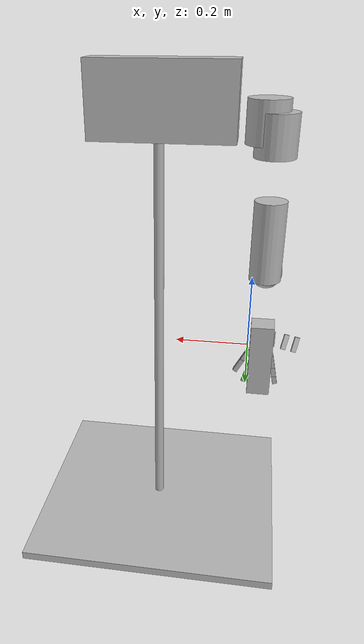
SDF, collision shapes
<?xml version='1.0'?>
<sdf version='1.6'>
  <model name='xolobot_arm'>
    <link name='link_hombro_alto_izq'>
      <inertial>
        <mass>1</mass>
        <inertia>
          <ixx>0.166667</ixx>
          <ixy>0</ixy>
          <ixz>0</ixz>
          <iyy>0.166667</iyy>
          <iyz>0</iyz>
          <izz>0.166667</izz>
        </inertia>
        <pose frame=''>0.01 0.01 0.04 0 -0 0</pose>
      </inertial>
      <pose frame=''>-0.009408 0.054088 0.601289 0 -0 0</pose>
      <gravity>1</gravity>
      <self_collide>0</self_collide>
      <kinematic>0</kinematic>
      <enable_wind>0</enable_wind>
      <visual name='visual'>
        <pose frame=''>0 0 0 0 -0 0</pose>
        <geometry>
          <mesh>
            <uri>model://meshes/hombro_alto.dae</uri>
            <scale>1 1 1</scale>
          </mesh>
        </geometry>
        <transparency>0</transparency>
        <cast_shadows>0</cast_shadows>
      </visual>
      <collision name='collision'>
        <laser_retro>0</laser_retro>
        <max_contacts>10</max_contacts>
        <pose frame=''>0 0 0 0 -0 0</pose>
        <geometry>
          <cylinder><radius>0.05</radius><length>0.10</length></cylinder>
        </geometry>
        <surface>
          <friction>
            <ode>
              <mu>1</mu>
              <mu2>1</mu2>
              <fdir1>0 0 0</fdir1>
              <slip1>0</slip1>
              <slip2>0</slip2>
            </ode>
            <torsional>
              <coefficient>1</coefficient>
              <patch_radius>0</patch_radius>
              <surface_radius>0</surface_radius>
              <use_patch_radius>1</use_patch_radius>
              <ode>
                <slip>0</slip>
              </ode>
            </torsional>
          </friction>
          <bounce>
            <restitution_coefficient>0</restitution_coefficient>
            <threshold>1e+06</threshold>
          </bounce>
          <contact>
            <collide_without_contact>0</collide_without_contact>
            <collide_without_contact_bitmask>1</collide_without_contact_bitmask>
            <collide_bitmask>1</collide_bitmask>
            <ode>
              <soft_cfm>0</soft_cfm>
              <soft_erp>0.2</soft_erp>
              <kp>1e+05</kp>
              <kd>1</kd>
              <max_vel>0.01</max_vel>
              <min_depth>0.001</min_depth>
            </ode>
            <bullet>
              <split_impulse>1</split_impulse>
              <split_impulse_penetration_threshold>-0.01</split_impulse_penetration_threshold>
              <soft_cfm>0</soft_cfm>
              <soft_erp>0.2</soft_erp>
              <kp>1e+05</kp>
              <kd>1</kd>
            </bullet>
          </contact>
        </surface>
      </collision>
    </link>
    <link name='link_hombro_bajo_izq'>
      <inertial>
        <mass>0.2</mass>
        <inertia>
          <ixx>0.166667</ixx>
          <ixy>0</ixy>
          <ixz>0</ixz>
          <iyy>0.166667</iyy>
          <iyz>0</iyz>
          <izz>0.166667</izz>
        </inertia>
        <pose frame=''>0 0 0.02 0 -0 0</pose>
      </inertial>
      <pose frame=''>-0.030348 0.063126 0.573568 0 -0 3.14159</pose>
      <gravity>1</gravity>
      <self_collide>0</self_collide>
      <kinematic>0</kinematic>
      <enable_wind>0</enable_wind>
      <visual name='visual'>
        <pose frame=''>0 0 0 0 -0 0</pose>
        <geometry>
          <mesh>
            <uri>model://meshes/hombro_bajo.dae</uri>
            <scale>1 1 1</scale>
          </mesh>
        </geometry>
        <transparency>0</transparency>
        <cast_shadows>0</cast_shadows>
      </visual>
      <collision name='collision'>
        <laser_retro>0</laser_retro>
        <max_contacts>10</max_contacts>
        <pose frame=''>0 0 0 0 -0 0</pose>
        <geometry>
          <cylinder><radius>0.05</radius><length>0.10</length></cylinder>
        </geometry>
        <surface>
          <friction>
            <ode>
              <mu>1</mu>
              <mu2>1</mu2>
              <fdir1>0 0 0</fdir1>
              <slip1>0</slip1>
              <slip2>0</slip2>
            </ode>
            <torsional>
              <coefficient>1</coefficient>
              <patch_radius>0</patch_radius>
              <surface_radius>0</surface_radius>
              <use_patch_radius>1</use_patch_radius>
              <ode>
                <slip>0</slip>
              </ode>
            </torsional>
          </friction>
          <bounce>
            <restitution_coefficient>0</restitution_coefficient>
            <threshold>1e+06</threshold>
          </bounce>
          <contact>
            <collide_without_contact>0</collide_without_contact>
            <collide_without_contact_bitmask>1</collide_without_contact_bitmask>
            <collide_bitmask>1</collide_bitmask>
            <ode>
              <soft_cfm>0</soft_cfm>
              <soft_erp>0.2</soft_erp>
              <kp>1e+05</kp>
              <kd>1</kd>
              <max_vel>0.01</max_vel>
              <min_depth>0.001</min_depth>
            </ode>
            <bullet>
              <split_impulse>1</split_impulse>
              <split_impulse_penetration_threshold>-0.01</split_impulse_penetration_threshold>
              <soft_cfm>0</soft_cfm>
              <soft_erp>0.2</soft_erp>
              <kp>1e+05</kp>
              <kd>1</kd>
            </bullet>
          </contact>
        </surface>
      </collision>
    </link>
    <link name='link_biceps_izq'>
      <inertial>
        <mass>1</mass>
        <inertia>
          <ixx>0.333333</ixx>
          <ixy>0</ixy>
          <ixz>0</ixz>
          <iyy>0.333333</iyy>
          <iyz>0</iyz>
          <izz>0.333333</izz>
        </inertia>
        <pose frame=''>0 0 0.17 0 -0 0</pose>
      </inertial>
      <pose frame=''>-0.030645 0.062763 0.323669 0 -0 0</pose>
      <gravity>1</gravity>
      <self_collide>0</self_collide>
      <kinematic>0</kinematic>
      <enable_wind>0</enable_wind>
      <visual name='visual'>
        <pose frame=''>0 0 0 0 -0 0</pose>
        <geometry>
          <mesh>
            <uri>model://meshes/biceps_izq.dae</uri>
            <scale>1 1 1</scale>
          </mesh>
        </geometry>
        <transparency>0</transparency>
        <cast_shadows>0</cast_shadows>
      </visual>
      <collision name='collision'>
        <laser_retro>0</laser_retro>
        <max_contacts>10</max_contacts>
        <pose frame=''>0 0 0 0 -0 0</pose>
        <geometry>
          <cylinder><radius>0.04</radius><length>0.20</length></cylinder>
        </geometry>
        <surface>
          <friction>
            <ode>
              <mu>1</mu>
              <mu2>1</mu2>
              <fdir1>0 0 0</fdir1>
              <slip1>0</slip1>
              <slip2>0</slip2>
            </ode>
            <torsional>
              <coefficient>1</coefficient>
              <patch_radius>0</patch_radius>
              <surface_radius>0</surface_radius>
              <use_patch_radius>1</use_patch_radius>
              <ode>
                <slip>0</slip>
              </ode>
            </torsional>
          </friction>
          <bounce>
            <restitution_coefficient>0</restitution_coefficient>
            <threshold>1e+06</threshold>
          </bounce>
          <contact>
            <collide_without_contact>0</collide_without_contact>
            <collide_without_contact_bitmask>1</collide_without_contact_bitmask>
            <collide_bitmask>1</collide_bitmask>
            <ode>
              <soft_cfm>0</soft_cfm>
              <soft_erp>0.2</soft_erp>
              <kp>1e+05</kp>
              <kd>1</kd>
              <max_vel>0.01</max_vel>
              <min_depth>0.001</min_depth>
            </ode>
            <bullet>
              <split_impulse>1</split_impulse>
              <split_impulse_penetration_threshold>-0.01</split_impulse_penetration_threshold>
              <soft_cfm>0</soft_cfm>
              <soft_erp>0.2</soft_erp>
              <kp>1e+05</kp>
              <kd>1</kd>
            </bullet>
          </contact>
        </surface>
      </collision>
    </link>
    <link name='link_codo_izq'>
      <inertial>
        <mass>0.2</mass>
        <inertia>
          <ixx>0.166667</ixx>
          <ixy>0</ixy>
          <ixz>0</ixz>
          <iyy>0.166667</iyy>
          <iyz>0</iyz>
          <izz>0.166667</izz>
        </inertia>
        <pose frame=''>0 0.012 0.03 0 -0 0</pose>
      </inertial>
      <pose frame=''>-0.033844 0.05112 0.238164 0 -0 0</pose>
      <gravity>1</gravity>
      <self_collide>0</self_collide>
      <kinematic>0</kinematic>
      <enable_wind>0</enable_wind>
      <visual name='visual'>
        <pose frame=''>0 0 0 0 -0 0</pose>
        <geometry>
          <mesh>
            <uri>model://meshes/codo_izq.dae</uri>
            <scale>1 1 1</scale>
          </mesh>
        </geometry>
        <transparency>0</transparency>
        <cast_shadows>0</cast_shadows>
      </visual>
      <collision name='collision'>
        <laser_retro>0</laser_retro>
        <max_contacts>10</max_contacts>
        <pose frame=''>0 0 0 0 -0 0</pose>
        <geometry>
          <sphere><radius>0.04</radius></sphere>
        </geometry>
        <surface>
          <friction>
            <ode>
              <mu>1</mu>
              <mu2>1</mu2>
              <fdir1>0 0 0</fdir1>
              <slip1>0</slip1>
              <slip2>0</slip2>
            </ode>
            <torsional>
              <coefficient>1</coefficient>
              <patch_radius>0</patch_radius>
              <surface_radius>0</surface_radius>
              <use_patch_radius>1</use_patch_radius>
              <ode>
                <slip>0</slip>
              </ode>
            </torsional>
          </friction>
          <bounce>
            <restitution_coefficient>0</restitution_coefficient>
            <threshold>1e+06</threshold>
          </bounce>
          <contact>
            <collide_without_contact>0</collide_without_contact>
            <collide_without_contact_bitmask>1</collide_without_contact_bitmask>
            <collide_bitmask>1</collide_bitmask>
            <ode>
              <soft_cfm>0</soft_cfm>
              <soft_erp>0.2</soft_erp>
              <kp>1e+05</kp>
              <kd>1</kd>
              <max_vel>0.01</max_vel>
              <min_depth>0.001</min_depth>
            </ode>
            <bullet>
              <split_impulse>1</split_impulse>
              <split_impulse_penetration_threshold>-0.01</split_impulse_penetration_threshold>
              <soft_cfm>0</soft_cfm>
              <soft_erp>0.2</soft_erp>
              <kp>1e+05</kp>
              <kd>1</kd>
            </bullet>
          </contact>
        </surface>
      </collision>
    </link>
    <link name='link_antebrazo_izq'>
      <inertial>
        <mass>1</mass>
        <inertia>
          <ixx>0.166667</ixx>
          <ixy>0</ixy>
          <ixz>0</ixz>
          <iyy>0.166667</iyy>
          <iyz>0</iyz>
          <izz>0.166667</izz>
        </inertia>
        <pose frame=''>0 0 0.15 0 -0 0</pose>
      </inertial>
      <pose frame=''>-0.03641 0.063676 0 0 -0 0</pose>
      <gravity>1</gravity>
      <self_collide>0</self_collide>
      <kinematic>0</kinematic>
      <enable_wind>0</enable_wind>
      <visual name='visual'>
        <pose frame=''>0 0 0 0 -0 0</pose>
        <geometry>
          <mesh>
            <uri>model://meshes/antebrazo_mano_izq.dae</uri>
            <scale>1 1 1</scale>
          </mesh>
        </geometry>
        <transparency>0</transparency>
        <cast_shadows>0</cast_shadows>
      </visual>
      <collision name='collision'>
        <laser_retro>0</laser_retro>
        <max_contacts>10</max_contacts>
        <pose frame=''>0 0 0 0 -0 0</pose>
        <geometry>
          <box><size>0.06 0.06 0.20</size></box>
        </geometry>
        <surface>
          <friction>
            <ode>
              <mu>5</mu>
              <mu2>5</mu2>
              <fdir1>0 0 0</fdir1>
              <slip1>0</slip1>
              <slip2>0</slip2>
            </ode>
            <torsional>
              <coefficient>1</coefficient>
              <patch_radius>0</patch_radius>
              <surface_radius>0</surface_radius>
              <use_patch_radius>1</use_patch_radius>
              <ode>
                <slip>0</slip>
              </ode>
            </torsional>
          </friction>
          <bounce>
            <restitution_coefficient>0</restitution_coefficient>
            <threshold>1e+06</threshold>
          </bounce>
          <contact>
            <collide_without_contact>0</collide_without_contact>
            <collide_without_contact_bitmask>1</collide_without_contact_bitmask>
            <collide_bitmask>1</collide_bitmask>
            <ode>
              <soft_cfm>0</soft_cfm>
              <soft_erp>0.2</soft_erp>
              <kp>1e+05</kp>
              <kd>1</kd>
              <max_vel>0.01</max_vel>
              <min_depth>0.001</min_depth>
            </ode>
            <bullet>
              <split_impulse>1</split_impulse>
              <split_impulse_penetration_threshold>-0.01</split_impulse_penetration_threshold>
              <soft_cfm>0</soft_cfm>
              <soft_erp>0.2</soft_erp>
              <kp>1e+05</kp>
              <kd>1</kd>
            </bullet>
          </contact>
        </surface>
      </collision>
      <sensor name="antebrazo_sensor" type="contact">
        <update_rate>10</update_rate>
        <contact>
          <collision>collision</collision>
        </contact>

      </sensor>
    </link>

    <link name='link_palma_izq'>
      <inertial>
        <mass>1</mass>
        <inertia>
          <ixx>0.166667</ixx>
          <ixy>0</ixy>
          <ixz>0</ixz>
          <iyy>0.166667</iyy>
          <iyz>0</iyz>
          <izz>0.166667</izz>
        </inertia>
        <pose frame=''>0 0 0.15 0 -0 0</pose>
      </inertial>
      <pose frame=''>-0.03641 0.063676 -0.001 0 -0 0</pose>
      <gravity>1</gravity>
      <self_collide>0</self_collide>
      <kinematic>0</kinematic>
      <enable_wind>0</enable_wind>
      <visual name='visual'>
        <pose frame=''>0 0 0 0 -0 0</pose>
        <geometry>
          <mesh>
            <uri>model://meshes/palma.dae</uri>
            <scale>1 1 1</scale>
          </mesh>
        </geometry>
        <transparency>0</transparency>
        <cast_shadows>0</cast_shadows>
      </visual>
      <collision name='collision'>
        <laser_retro>0</laser_retro>
        <max_contacts>10</max_contacts>
        <pose frame=''>0 0 0 0 -0 0</pose>
        <geometry>
          <box><size>0.06 0.06 0.025</size></box>
        </geometry>
        <surface>
          <friction>
            <ode>
              <mu>10</mu>
              <mu2>10</mu2>
              <fdir1>0 0 0</fdir1>
              <slip1>0</slip1>
              <slip2>0</slip2>
            </ode>
            <torsional>
              <coefficient>1</coefficient>
              <patch_radius>0</patch_radius>
              <surface_radius>0</surface_radius>
              <use_patch_radius>1</use_patch_radius>
              <ode>
                <slip>0</slip>
              </ode>
            </torsional>
          </friction>
          <bounce>
            <restitution_coefficient>0</restitution_coefficient>
            <threshold>1e+06</threshold>
          </bounce>
          <contact>
            <collide_without_contact>0</collide_without_contact>
            <collide_without_contact_bitmask>1</collide_without_contact_bitmask>
            <collide_bitmask>1</collide_bitmask>
            <ode>
              <soft_cfm>0.01</soft_cfm>
              <soft_erp>0.8</soft_erp>
              <kp>1e+05</kp>
              <kd>1</kd>
              <max_vel>0.01</max_vel>
              <min_depth>0.001</min_depth>
            </ode>
            <bullet>
              <split_impulse>1</split_impulse>
              <split_impulse_penetration_threshold>-0.01</split_impulse_penetration_threshold>
              <soft_cfm>0</soft_cfm>
              <soft_erp>0.2</soft_erp>
              <kp>1e+05</kp>
              <kd>1</kd>
            </bullet>
          </contact>
        </surface>
      </collision>
      <sensor name="palma_sensor" type="contact">
        <update_rate>10</update_rate>
        <contact>
          <collision>collision</collision>
        </contact>

      </sensor>
    </link>

    <link name='link_pulgar_1_izq'>
      <inertial>
        <mass>0.02</mass>
        <inertia>
          <ixx>0.166667</ixx>
          <ixy>0</ixy>
          <ixz>0</ixz>
          <iyy>0.166667</iyy>
          <iyz>0</iyz>
          <izz>0.166667</izz>
        </inertia>
        <pose frame=''>0 0 0.01 0 -0 0</pose>
      </inertial>
      <pose frame=''>-0.064591 0.063564 0.056306 0 0 0</pose>
      <gravity>1</gravity>
      <self_collide>0</self_collide>
      <kinematic>0</kinematic>
      <enable_wind>0</enable_wind>
      <visual name='visual'>
        <pose frame=''>0 0 0 0 -0 0</pose>
        <geometry>
          <mesh>
            <uri>model://meshes/dedos/pulgar_1_izq.dae</uri>
            <scale>1 1 1</scale>
          </mesh>
        </geometry>
        <transparency>0</transparency>
        <cast_shadows>0</cast_shadows>
      </visual>
      <collision name='collision'>
        <laser_retro>0</laser_retro>
        <max_contacts>10</max_contacts>
        <pose frame=''>0 0 0 0 -0 0</pose>
        <geometry>
          <box><size>0.012 0.012 0.04</size></box>
        </geometry>
        <surface>
          <friction>
            <ode>
              <mu>10</mu>
              <mu2>10</mu2>
              <fdir1>0 0 0</fdir1>
              <slip1>0</slip1>
              <slip2>0</slip2>
            </ode>
            <torsional>
              <coefficient>1</coefficient>
              <patch_radius>0</patch_radius>
              <surface_radius>0</surface_radius>
              <use_patch_radius>1</use_patch_radius>
              <ode>
                <slip>0</slip>
              </ode>
            </torsional>
          </friction>
          <bounce>
            <restitution_coefficient>0</restitution_coefficient>
            <threshold>1e+06</threshold>
          </bounce>
          <contact>
            <collide_without_contact>0</collide_without_contact>
            <collide_without_contact_bitmask>1</collide_without_contact_bitmask>
            <collide_bitmask>1</collide_bitmask>
            <ode>
              <soft_cfm>0</soft_cfm>
              <soft_erp>0.2</soft_erp>
              <kp>1e+05</kp>
              <kd>1</kd>
              <max_vel>0.01</max_vel>
              <min_depth>0.001</min_depth>
            </ode>
            <bullet>
              <split_impulse>1</split_impulse>
              <split_impulse_penetration_threshold>-0.01</split_impulse_penetration_threshold>
              <soft_cfm>0</soft_cfm>
              <soft_erp>0.2</soft_erp>
              <kp>1e+05</kp>
              <kd>1</kd>
            </bullet>
          </contact>
        </surface>
      </collision>
    </link>
    <link name='link_pulgar_2_izq'>
      <inertial>
        <mass>0.02</mass>
        <inertia>
          <ixx>0.166667</ixx>
          <ixy>0</ixy>
          <ixz>0</ixz>
          <iyy>0.166667</iyy>
          <iyz>0</iyz>
          <izz>0.166667</izz>
        </inertia>
        <pose frame=''>0 0 0.009 0 -0 0</pose>
      </inertial>
      <pose frame=''>-0.096881 0.06868 0.052774 0.38 -0.238 0</pose>
      <gravity>1</gravity>
      <self_collide>0</self_collide>
      <kinematic>0</kinematic>
      <enable_wind>0</enable_wind>
      <visual name='visual'>
        <pose frame=''>0 0 0 0 -0 0</pose>
        <geometry>
          <mesh>
            <uri>model://meshes/dedos/pulgar_2.dae</uri>
            <scale>1 1 1</scale>
          </mesh>
        </geometry>
        <transparency>0</transparency>
        <cast_shadows>0</cast_shadows>
      </visual>
      <collision name='collision'>
        <laser_retro>0</laser_retro>
        <max_contacts>10</max_contacts>
        <pose frame=''>0 0 0 0 -0 0</pose>
        <geometry>
          <box><size>0.012 0.012 0.04</size></box>
        </geometry>
        <surface>
          <friction>
            <ode>
              <mu>10</mu>
              <mu2>10</mu2>
              <fdir1>0 0 0</fdir1>
              <slip1>0</slip1>
              <slip2>0</slip2>
            </ode>
            <torsional>
              <coefficient>1</coefficient>
              <patch_radius>0</patch_radius>
              <surface_radius>0</surface_radius>
              <use_patch_radius>1</use_patch_radius>
              <ode>
                <slip>0</slip>
              </ode>
            </torsional>
          </friction>
          <bounce>
            <restitution_coefficient>0</restitution_coefficient>
            <threshold>1e+06</threshold>
          </bounce>
          <contact>
            <collide_without_contact>0</collide_without_contact>
            <collide_without_contact_bitmask>1</collide_without_contact_bitmask>
            <collide_bitmask>1</collide_bitmask>
            <ode>
              <soft_cfm>0</soft_cfm>
              <soft_erp>0.2</soft_erp>
              <kp>1e+05</kp>
              <kd>1</kd>
              <max_vel>0.01</max_vel>
              <min_depth>0.001</min_depth>
            </ode>
            <bullet>
              <split_impulse>1</split_impulse>
              <split_impulse_penetration_threshold>-0.01</split_impulse_penetration_threshold>
              <soft_cfm>0</soft_cfm>
              <soft_erp>0.2</soft_erp>
              <kp>1e+05</kp>
              <kd>1</kd>
            </bullet>
          </contact>
        </surface>
      </collision>
    </link>
    <link name='link_pulgar_3_izq'>
      <inertial>
        <mass>0.02</mass>
        <inertia>
          <ixx>0.166667</ixx>
          <ixy>0</ixy>
          <ixz>0</ixz>
          <iyy>0.166667</iyy>
          <iyz>0</iyz>
          <izz>0.166667</izz>
        </inertia>
        <pose frame=''>0 0 0.008 0 -0 0</pose>
      </inertial>
      <pose frame=''>-0.124299 0.06845 0.047056 -0.37 0.23 3.14159</pose>
      <gravity>1</gravity>
      <self_collide>0</self_collide>
      <kinematic>0</kinematic>
      <enable_wind>0</enable_wind>
      <visual name='visual'>
        <pose frame=''>0 0 0 0 -0 0</pose>
        <geometry>
          <mesh>
            <uri>model://meshes/dedos/pulgar_3.dae</uri>
            <scale>1 1 1</scale>
          </mesh>
        </geometry>
        <transparency>0</transparency>
        <cast_shadows>0</cast_shadows>
      </visual>
      <collision name='collision'>
        <laser_retro>0</laser_retro>
        <max_contacts>10</max_contacts>
        <pose frame=''>0 0 0 0 -0 0</pose>
        <geometry>
          <box><size>0.012 0.012 0.04</size></box>
        </geometry>
        <surface>
          <friction>
            <ode>
              <mu>10</mu>
              <mu2>10</mu2>
              <fdir1>0 0 0</fdir1>
              <slip1>0</slip1>
              <slip2>0</slip2>
            </ode>
            <torsional>
              <coefficient>1</coefficient>
              <patch_radius>0</patch_radius>
              <surface_radius>0</surface_radius>
              <use_patch_radius>1</use_patch_radius>
              <ode>
                <slip>0</slip>
              </ode>
            </torsional>
          </friction>
          <bounce>
            <restitution_coefficient>0</restitution_coefficient>
            <threshold>1e+06</threshold>
          </bounce>
          <contact>
            <collide_without_contact>0</collide_without_contact>
            <collide_without_contact_bitmask>1</collide_without_contact_bitmask>
            <collide_bitmask>1</collide_bitmask>
            <ode>
              <soft_cfm>0</soft_cfm>
              <soft_erp>0.2</soft_erp>
              <kp>1e+05</kp>
              <kd>1</kd>
              <max_vel>0.01</max_vel>
              <min_depth>0.001</min_depth>
            </ode>
            <bullet>
              <split_impulse>1</split_impulse>
              <split_impulse_penetration_threshold>-0.01</split_impulse_penetration_threshold>
              <soft_cfm>0</soft_cfm>
              <soft_erp>0.2</soft_erp>
              <kp>1e+05</kp>
              <kd>1</kd>
            </bullet>
          </contact>
        </surface>
      </collision>
      <!--BUMPER PULGAR-->
      <sensor name="pulgar_3_sensor" type="contact">
        <update_rate>10</update_rate>
        <contact>
          <collision>collision</collision>
        </contact>

      </sensor>
    </link>
    <!--Dedo indice-->
    <link name='link_indice_1_izq'>
      <inertial>
        <mass>0.02</mass>
        <inertia>
          <ixx>0.166667</ixx>
          <ixy>0</ixy>
          <ixz>0</ixz>
          <iyy>0.166667</iyy>
          <iyz>0</iyz>
          <izz>0.166667</izz>
        </inertia>
        <pose frame=''>0 0 0 0 -0 0</pose>
      </inertial>
      <pose frame=''>-0.068102 0.0642 -0.009778 0 0.19 0</pose>
      <gravity>1</gravity>
      <self_collide>0</self_collide>
      <kinematic>0</kinematic>
      <enable_wind>0</enable_wind>
      <visual name='visual'>
        <pose frame=''>0 0 0 0 -0 0</pose>
        <geometry>
          <mesh>
            <uri>model://meshes/dedos/dedo_indice_1.dae</uri>
            <scale>1 1 1</scale>
          </mesh>
        </geometry>
        <transparency>0</transparency>
        <cast_shadows>0</cast_shadows>
      </visual>
      <collision name='collision'>
        <laser_retro>0</laser_retro>
        <max_contacts>10</max_contacts>
        <pose frame=''>0 0 0 0 -0 0</pose>
        <geometry>
          <box><size>0.012 0.012 0.04</size></box>
        </geometry>
        <surface>
          <friction>
            <ode>
              <mu>10</mu>
              <mu2>10</mu2>
              <fdir1>0 0 0</fdir1>
              <slip1>0</slip1>
              <slip2>0</slip2>
            </ode>
            <torsional>
              <coefficient>1</coefficient>
              <patch_radius>0</patch_radius>
              <surface_radius>0</surface_radius>
              <use_patch_radius>1</use_patch_radius>
              <ode>
                <slip>0</slip>
              </ode>
            </torsional>
          </friction>
          <bounce>
            <restitution_coefficient>0</restitution_coefficient>
            <threshold>1e+06</threshold>
          </bounce>
          <contact>
            <collide_without_contact>0</collide_without_contact>
            <collide_without_contact_bitmask>1</collide_without_contact_bitmask>
            <collide_bitmask>1</collide_bitmask>
            <ode>
              <soft_cfm>0</soft_cfm>
              <soft_erp>0.2</soft_erp>
              <kp>1e+05</kp>
              <kd>1</kd>
              <max_vel>0.01</max_vel>
              <min_depth>0.001</min_depth>
            </ode>
            <bullet>
              <split_impulse>1</split_impulse>
              <split_impulse_penetration_threshold>-0.01</split_impulse_penetration_threshold>
              <soft_cfm>0</soft_cfm>
              <soft_erp>0.2</soft_erp>
              <kp>1e+05</kp>
              <kd>1</kd>
            </bullet>
          </contact>
        </surface>
      </collision>
    </link>
    <link name='link_indice_2_izq'>
      <inertial>
        <mass>0.02</mass>
        <inertia>
          <ixx>0.166667</ixx>
          <ixy>0</ixy>
          <ixz>0</ixz>
          <iyy>0.166667</iyy>
          <iyz>0</iyz>
          <izz>0.166667</izz>
        </inertia>
        <pose frame=''>0 0 0 0 -0 0</pose>
      </inertial>
      <pose frame=''>-0.07306 0.0642 -0.035527 0 0.19 0</pose>
      <gravity>1</gravity>
      <self_collide>0</self_collide>
      <kinematic>0</kinematic>
      <enable_wind>0</enable_wind>
      <visual name='visual'>
        <pose frame=''>0 0 0 0 -0 0</pose>
        <geometry>
          <mesh>
            <uri>model://meshes/dedos/dedo_indice_2.dae</uri>
            <scale>1 1 1</scale>
          </mesh>
        </geometry>
        <transparency>0</transparency>
        <cast_shadows>0</cast_shadows>
      </visual>
      <collision name='collision'>
        <laser_retro>0</laser_retro>
        <max_contacts>10</max_contacts>
        <pose frame=''>0 0 0 0 -0 0</pose>
        <geometry>
          <box><size>0.012 0.012 0.04</size></box>
        </geometry>
        <surface>
          <friction>
            <ode>
              <mu>10</mu>
              <mu2>10</mu2>
              <fdir1>0 0 0</fdir1>
              <slip1>0</slip1>
              <slip2>0</slip2>
            </ode>
            <torsional>
              <coefficient>1</coefficient>
              <patch_radius>0</patch_radius>
              <surface_radius>0</surface_radius>
              <use_patch_radius>1</use_patch_radius>
              <ode>
                <slip>0</slip>
              </ode>
            </torsional>
          </friction>
          <bounce>
            <restitution_coefficient>0</restitution_coefficient>
            <threshold>1e+06</threshold>
          </bounce>
          <contact>
            <collide_without_contact>0</collide_without_contact>
            <collide_without_contact_bitmask>1</collide_without_contact_bitmask>
            <collide_bitmask>1</collide_bitmask>
            <ode>
              <soft_cfm>0</soft_cfm>
              <soft_erp>0.2</soft_erp>
              <kp>1e+05</kp>
              <kd>1</kd>
              <max_vel>0.01</max_vel>
              <min_depth>0.001</min_depth>
            </ode>
            <bullet>
              <split_impulse>1</split_impulse>
              <split_impulse_penetration_threshold>-0.01</split_impulse_penetration_threshold>
              <soft_cfm>0</soft_cfm>
              <soft_erp>0.2</soft_erp>
              <kp>1e+05</kp>
              <kd>1</kd>
            </bullet>
          </contact>
        </surface>
      </collision>
    </link>
    <link name='link_indice_3_izq'>
      <inertial>
        <mass>0.02</mass>
        <inertia>
          <ixx>0.166667</ixx>
          <ixy>0</ixy>
          <ixz>0</ixz>
          <iyy>0.166667</iyy>
          <iyz>0</iyz>
          <izz>0.166667</izz>
        </inertia>
        <pose frame=''>0 0 0 0 -0 0</pose>
      </inertial>
      <pose frame=''>-0.077462 0.0642 -0.058286 0 0.19 0</pose>
      <gravity>1</gravity>
      <self_collide>0</self_collide>
      <kinematic>0</kinematic>
      <enable_wind>0</enable_wind>
      <visual name='visual'>
        <pose frame=''>0 0 0 0 -0 0</pose>
        <geometry>
          <mesh>
            <uri>model://meshes/dedos/dedo_indice_3.dae</uri>
            <scale>1 1 1</scale>
          </mesh>
        </geometry>
        <transparency>0</transparency>
        <cast_shadows>0</cast_shadows>
      </visual>
      <collision name='collision'>
        <laser_retro>0</laser_retro>
        <max_contacts>10</max_contacts>
        <pose frame=''>0 0 0 0 -0 0</pose>
        <geometry>
          <box><size>0.012 0.012 0.04</size></box>
        </geometry>
        <surface>
          <friction>
            <ode>
              <mu>10</mu>
              <mu2>10</mu2>
              <fdir1>0 0 0</fdir1>
              <slip1>0</slip1>
              <slip2>0</slip2>
            </ode>
            <torsional>
              <coefficient>1</coefficient>
              <patch_radius>0</patch_radius>
              <surface_radius>0</surface_radius>
              <use_patch_radius>1</use_patch_radius>
              <ode>
                <slip>0</slip>
              </ode>
            </torsional>
          </friction>
          <bounce>
            <restitution_coefficient>0</restitution_coefficient>
            <threshold>1e+06</threshold>
          </bounce>
          <contact>
            <collide_without_contact>0</collide_without_contact>
            <collide_without_contact_bitmask>1</collide_without_contact_bitmask>
            <collide_bitmask>1</collide_bitmask>
            <ode>
              <soft_cfm>0</soft_cfm>
              <soft_erp>0.2</soft_erp>
              <kp>1e+05</kp>
              <kd>1</kd>
              <max_vel>0.01</max_vel>
              <min_depth>0.001</min_depth>
            </ode>
            <bullet>
              <split_impulse>1</split_impulse>
              <split_impulse_penetration_threshold>-0.01</split_impulse_penetration_threshold>
              <soft_cfm>0</soft_cfm>
              <soft_erp>0.2</soft_erp>
              <kp>1e+05</kp>
              <kd>1</kd>
            </bullet>
          </contact>
        </surface>
      </collision>
      <!--Bumper Indice-->
      <sensor name="indice_3_sensor" type="contact">
        <update_rate>10</update_rate>
        <contact>
          <collision>collision</collision>
        </contact>

      </sensor>
    </link>
    <link name='link_cordial_1_izq'>
      <inertial>
        <mass>0.02</mass>
        <inertia>
          <ixx>0.166667</ixx>
          <ixy>0</ixy>
          <ixz>0</ixz>
          <iyy>0.166667</iyy>
          <iyz>0</iyz>
          <izz>0.166667</izz>
        </inertia>
        <pose frame=''>0 0 0 0 -0 0</pose>
      </inertial>
      <pose frame=''>-0.040491 0.063627 -0.013835 0 -0.101 0</pose>
      <gravity>1</gravity>
      <self_collide>0</self_collide>
      <kinematic>0</kinematic>
      <enable_wind>0</enable_wind>
      <visual name='visual'>
        <pose frame=''>0 0 0 0 -0 0</pose>
        <geometry>
          <mesh>
            <uri>model://meshes/dedos/dedo_cordial_1.dae</uri>
            <scale>1 1 1</scale>
          </mesh>
        </geometry>
        <transparency>0</transparency>
        <cast_shadows>0</cast_shadows>
      </visual>
      <collision name='collision'>
        <laser_retro>0</laser_retro>
        <max_contacts>10</max_contacts>
        <pose frame=''>0 0 0 0 -0 0</pose>
        <geometry>
          <box><size>0.012 0.012 0.04</size></box>
        </geometry>
        <surface>
          <friction>
            <ode>
              <mu>10</mu>
              <mu2>10</mu2>
              <fdir1>0 0 0</fdir1>
              <slip1>0</slip1>
              <slip2>0</slip2>
            </ode>
            <torsional>
              <coefficient>1</coefficient>
              <patch_radius>0</patch_radius>
              <surface_radius>0</surface_radius>
              <use_patch_radius>1</use_patch_radius>
              <ode>
                <slip>0</slip>
              </ode>
            </torsional>
          </friction>
          <bounce>
            <restitution_coefficient>0</restitution_coefficient>
            <threshold>1e+06</threshold>
          </bounce>
          <contact>
            <collide_without_contact>0</collide_without_contact>
            <collide_without_contact_bitmask>1</collide_without_contact_bitmask>
            <collide_bitmask>1</collide_bitmask>
            <ode>
              <soft_cfm>0</soft_cfm>
              <soft_erp>0.2</soft_erp>
              <kp>1e+05</kp>
              <kd>1</kd>
              <max_vel>0.01</max_vel>
              <min_depth>0.001</min_depth>
            </ode>
            <bullet>
              <split_impulse>1</split_impulse>
              <split_impulse_penetration_threshold>-0.01</split_impulse_penetration_threshold>
              <soft_cfm>0</soft_cfm>
              <soft_erp>0.2</soft_erp>
              <kp>1e+05</kp>
              <kd>1</kd>
            </bullet>
          </contact>
        </surface>
      </collision>
    </link>
    <link name='link_cordial_2_izq'>
      <inertial>
        <mass>0.02</mass>
        <inertia>
          <ixx>0.166667</ixx>
          <ixy>0</ixy>
          <ixz>0</ixz>
          <iyy>0.166667</iyy>
          <iyz>0</iyz>
          <izz>0.166667</izz>
        </inertia>
        <pose frame=''>0 0 0 0 -0 0</pose>
      </inertial>
      <pose frame=''>-0.037353 0.063627 -0.045105 0 -0.101 0</pose>
      <gravity>1</gravity>
      <self_collide>0</self_collide>
      <kinematic>0</kinematic>
      <enable_wind>0</enable_wind>
      <visual name='visual'>
        <pose frame=''>0 0 0 0 -0 0</pose>
        <geometry>
          <mesh>
            <uri>model://meshes/dedos/dedo_cordial_2.dae</uri>
            <scale>1 1 1</scale>
          </mesh>
        </geometry>
        <transparency>0</transparency>
        <cast_shadows>0</cast_shadows>
      </visual>
      <collision name='collision'>
        <laser_retro>0</laser_retro>
        <max_contacts>10</max_contacts>
        <pose frame=''>0 0 0 0 -0 0</pose>
        <geometry>
          <box><size>0.012 0.012 0.04</size></box>
        </geometry>
        <surface>
          <friction>
            <ode>
              <mu>10</mu>
              <mu2>10</mu2>
              <fdir1>0 0 0</fdir1>
              <slip1>0</slip1>
              <slip2>0</slip2>
            </ode>
            <torsional>
              <coefficient>1</coefficient>
              <patch_radius>0</patch_radius>
              <surface_radius>0</surface_radius>
              <use_patch_radius>1</use_patch_radius>
              <ode>
                <slip>0</slip>
              </ode>
            </torsional>
          </friction>
          <bounce>
            <restitution_coefficient>0</restitution_coefficient>
            <threshold>1e+06</threshold>
          </bounce>
          <contact>
            <collide_without_contact>0</collide_without_contact>
            <collide_without_contact_bitmask>1</collide_without_contact_bitmask>
            <collide_bitmask>1</collide_bitmask>
            <ode>
              <soft_cfm>0</soft_cfm>
              <soft_erp>0.2</soft_erp>
              <kp>1e+05</kp>
              <kd>1</kd>
              <max_vel>0.01</max_vel>
              <min_depth>0.001</min_depth>
            </ode>
            <bullet>
              <split_impulse>1</split_impulse>
              <split_impulse_penetration_threshold>-0.01</split_impulse_penetration_threshold>
              <soft_cfm>0</soft_cfm>
              <soft_erp>0.2</soft_erp>
              <kp>1e+05</kp>
              <kd>1</kd>
            </bullet>
          </contact>
        </surface>
      </collision>
    </link>
    <link name='link_cordial_3_izq'>
      <inertial>
        <mass>0.02</mass>
        <inertia>
          <ixx>0.166667</ixx>
          <ixy>0</ixy>
          <ixz>0</ixz>
          <iyy>0.166667</iyy>
          <iyz>0</iyz>
          <izz>0.166667</izz>
        </inertia>
        <pose frame=''>0 0 0 0 -0 0</pose>
      </inertial>
      <pose frame=''>-0.034636 0.063627 -0.07184 0 -0.101 0</pose>
      <gravity>1</gravity>
      <self_collide>0</self_collide>
      <kinematic>0</kinematic>
      <enable_wind>0</enable_wind>
      <visual name='visual'>
        <pose frame=''>0 0 0 0 -0 0</pose>
        <geometry>
          <mesh>
            <uri>model://meshes/dedos/dedo_cordial_3.dae</uri>
            <scale>1 1 1</scale>
          </mesh>
        </geometry>
        <transparency>0</transparency>
        <cast_shadows>0</cast_shadows>
      </visual>
      <collision name='collision'>
        <laser_retro>0</laser_retro>
        <max_contacts>10</max_contacts>
        <pose frame=''>0 0 0 0 -0 0</pose>
        <geometry>
          <box><size>0.012 0.012 0.04</size></box>
        </geometry>
        <surface>
          <friction>
            <ode>
              <mu>10</mu>
              <mu2>10</mu2>
              <fdir1>0 0 0</fdir1>
              <slip1>0</slip1>
              <slip2>0</slip2>
            </ode>
            <torsional>
              <coefficient>1</coefficient>
              <patch_radius>0</patch_radius>
              <surface_radius>0</surface_radius>
              <use_patch_radius>1</use_patch_radius>
              <ode>
                <slip>0</slip>
              </ode>
            </torsional>
          </friction>
          <bounce>
            <restitution_coefficient>0</restitution_coefficient>
            <threshold>1e+06</threshold>
          </bounce>
          <contact>
            <collide_without_contact>0</collide_without_contact>
            <collide_without_contact_bitmask>1</collide_without_contact_bitmask>
            <collide_bitmask>1</collide_bitmask>
            <ode>
              <soft_cfm>0</soft_cfm>
              <soft_erp>0.2</soft_erp>
              <kp>1e+05</kp>
              <kd>1</kd>
              <max_vel>0.01</max_vel>
              <min_depth>0.001</min_depth>
            </ode>
            <bullet>
              <split_impulse>1</split_impulse>
              <split_impulse_penetration_threshold>-0.01</split_impulse_penetration_threshold>
              <soft_cfm>0</soft_cfm>
              <soft_erp>0.2</soft_erp>
              <kp>1e+05</kp>
              <kd>1</kd>
            </bullet>
          </contact>
        </surface>
      </collision>
      <!--BUMPER CORDIAL-->
      <sensor name="cordial_3_sensor" type="contact">
        <update_rate>10</update_rate>
        <contact>
          <collision>collision</collision>
        </contact>

      </sensor>
    </link>
    <link name='link_anular_1_izq'>
      <inertial>
        <mass>0.02</mass>
        <inertia>
          <ixx>0.166667</ixx>
          <ixy>0</ixy>
          <ixz>0</ixz>
          <iyy>0.166667</iyy>
          <iyz>0</iyz>
          <izz>0.166667</izz>
        </inertia>
        <pose frame=''>0 0 0 0 -0 0</pose>
      </inertial>
      <pose frame=''>-0.0164 0.064056 -0.0076 0 -0.29 0</pose>
      <gravity>1</gravity>
      <self_collide>0</self_collide>
      <kinematic>0</kinematic>
      <enable_wind>0</enable_wind>
      <visual name='visual'>
        <pose frame=''>0 0 0 0 -0 0</pose>
        <geometry>
          <mesh>
            <uri>model://meshes/dedos/dedo_anular_1.dae</uri>
            <scale>1 1 1</scale>
          </mesh>
        </geometry>
        <transparency>0</transparency>
        <cast_shadows>0</cast_shadows>
      </visual>
      <collision name='collision'>
        <laser_retro>0</laser_retro>
        <max_contacts>10</max_contacts>
        <pose frame=''>0 0 0 0 -0 0</pose>
        <geometry>
          <box><size>0.012 0.012 0.04</size></box>
        </geometry>
        <surface>
          <friction>
            <ode>
              <mu>10</mu>
              <mu2>10</mu2>
              <fdir1>0 0 0</fdir1>
              <slip1>0</slip1>
              <slip2>0</slip2>
            </ode>
            <torsional>
              <coefficient>1</coefficient>
              <patch_radius>0</patch_radius>
              <surface_radius>0</surface_radius>
              <use_patch_radius>1</use_patch_radius>
              <ode>
                <slip>0</slip>
              </ode>
            </torsional>
          </friction>
          <bounce>
            <restitution_coefficient>0</restitution_coefficient>
            <threshold>1e+06</threshold>
          </bounce>
          <contact>
            <collide_without_contact>0</collide_without_contact>
            <collide_without_contact_bitmask>1</collide_without_contact_bitmask>
            <collide_bitmask>1</collide_bitmask>
            <ode>
              <soft_cfm>0</soft_cfm>
              <soft_erp>0.2</soft_erp>
              <kp>1e+05</kp>
              <kd>1</kd>
              <max_vel>0.01</max_vel>
              <min_depth>0.001</min_depth>
            </ode>
            <bullet>
              <split_impulse>1</split_impulse>
              <split_impulse_penetration_threshold>-0.01</split_impulse_penetration_threshold>
              <soft_cfm>0</soft_cfm>
              <soft_erp>0.2</soft_erp>
              <kp>1e+05</kp>
              <kd>1</kd>
            </bullet>
          </contact>
        </surface>
      </collision>
    </link>
    <link name='link_anular_2_izq'>
      <inertial>
        <mass>0.02</mass>
        <inertia>
          <ixx>0.166667</ixx>
          <ixy>0</ixy>
          <ixz>0</ixz>
          <iyy>0.166667</iyy>
          <iyz>0</iyz>
          <izz>0.166667</izz>
        </inertia>
        <pose frame=''>0 0 0 0 -0 0</pose>
      </inertial>
      <pose frame=''>-0.008328 0.064056 -0.03484 0 -0.29 0</pose>
      <self_collide>0</self_collide>
      <enable_wind>0</enable_wind>
      <kinematic>0</kinematic>
      <gravity>1</gravity>
      <visual name='visual'>
        <pose frame=''>0 0 0 0 -0 0</pose>
        <geometry>
          <mesh>
            <uri>model://meshes/dedos/dedo_anular_2.dae</uri>
            <scale>1 1 1</scale>
          </mesh>
        </geometry>
        <transparency>0</transparency>
        <cast_shadows>0</cast_shadows>
      </visual>
      <collision name='collision'>
        <laser_retro>0</laser_retro>
        <max_contacts>10</max_contacts>
        <pose frame=''>0 0 0 0 -0 0</pose>
        <geometry>
          <box><size>0.012 0.012 0.04</size></box>
        </geometry>
        <surface>
          <friction>
            <ode>
              <mu>10</mu>
              <mu2>10</mu2>
              <fdir1>0 0 0</fdir1>
              <slip1>0</slip1>
              <slip2>0</slip2>
            </ode>
            <torsional>
              <coefficient>1</coefficient>
              <patch_radius>0</patch_radius>
              <surface_radius>0</surface_radius>
              <use_patch_radius>1</use_patch_radius>
              <ode>
                <slip>0</slip>
              </ode>
            </torsional>
          </friction>
          <bounce>
            <restitution_coefficient>0</restitution_coefficient>
            <threshold>1e+06</threshold>
          </bounce>
          <contact>
            <collide_without_contact>0</collide_without_contact>
            <collide_without_contact_bitmask>1</collide_without_contact_bitmask>
            <collide_bitmask>1</collide_bitmask>
            <ode>
              <soft_cfm>0</soft_cfm>
              <soft_erp>0.2</soft_erp>
              <kp>1e+05</kp>
              <kd>1</kd>
              <max_vel>0.01</max_vel>
              <min_depth>0.001</min_depth>
            </ode>
            <bullet>
              <split_impulse>1</split_impulse>
              <split_impulse_penetration_threshold>-0.01</split_impulse_penetration_threshold>
              <soft_cfm>0</soft_cfm>
              <soft_erp>0.2</soft_erp>
              <kp>1e+05</kp>
              <kd>1</kd>
            </bullet>
          </contact>
        </surface>
      </collision>
    </link>
    <link name='link_anular_3_izq'>
      <inertial>
        <mass>0.02</mass>
        <inertia>
          <ixx>0.166667</ixx>
          <ixy>0</ixy>
          <ixz>0</ixz>
          <iyy>0.166667</iyy>
          <iyz>0</iyz>
          <izz>0.166667</izz>
        </inertia>
        <pose frame=''>0 0 0 0 -0 0</pose>
      </inertial>
      <pose frame=''>-0.001153 0.064056 -0.058906 0 -0.29 0</pose>
      <self_collide>0</self_collide>
      <enable_wind>0</enable_wind>
      <kinematic>0</kinematic>
      <gravity>1</gravity>
      <visual name='visual'>
        <pose frame=''>0 0 0 0 -0 0</pose>
        <geometry>
          <mesh>
            <uri>model://meshes/dedos/dedo_anular_3.dae</uri>
            <scale>1 1 1</scale>
          </mesh>
        </geometry>
        <transparency>0</transparency>
        <cast_shadows>0</cast_shadows>
      </visual>
      <collision name='collision'>
        <laser_retro>0</laser_retro>
        <max_contacts>10</max_contacts>
        <pose frame=''>0 0 0 0 -0 0</pose>
        <geometry>
          <box><size>0.012 0.012 0.04</size></box>
        </geometry>
        <surface>
          <friction>
            <ode>
              <mu>10</mu>
              <mu2>10</mu2>
              <fdir1>0 0 0</fdir1>
              <slip1>0</slip1>
              <slip2>0</slip2>
            </ode>
            <torsional>
              <coefficient>1</coefficient>
              <patch_radius>0</patch_radius>
              <surface_radius>0</surface_radius>
              <use_patch_radius>1</use_patch_radius>
              <ode>
                <slip>0</slip>
              </ode>
            </torsional>
          </friction>
          <bounce>
            <restitution_coefficient>0</restitution_coefficient>
            <threshold>1e+06</threshold>
          </bounce>
          <contact>
            <collide_without_contact>0</collide_without_contact>
            <collide_without_contact_bitmask>1</collide_without_contact_bitmask>
            <collide_bitmask>1</collide_bitmask>
            <ode>
              <soft_cfm>0</soft_cfm>
              <soft_erp>0.2</soft_erp>
              <kp>1e+05</kp>
              <kd>1</kd>
              <max_vel>0.01</max_vel>
              <min_depth>0.001</min_depth>
            </ode>
            <bullet>
              <split_impulse>1</split_impulse>
              <split_impulse_penetration_threshold>-0.01</split_impulse_penetration_threshold>
              <soft_cfm>0</soft_cfm>
              <soft_erp>0.2</soft_erp>
              <kp>1e+05</kp>
              <kd>1</kd>
            </bullet>
          </contact>
        </surface>
      </collision>
      <!--BUMPER ANULAR-->
      <sensor name="anular_3_sensor" type="contact">
        <update_rate>10</update_rate>
        <contact>
          <collision>collision</collision>
        </contact>

      </sensor>
    </link>
    <link name='link_menique_1_izq'>
      <inertial>
        <mass>0.02</mass>
        <inertia>
          <ixx>0.166667</ixx>
          <ixy>0</ixy>
          <ixz>0</ixz>
          <iyy>0.166667</iyy>
          <iyz>0</iyz>
          <izz>0.166667</izz>
        </inertia>
        <pose frame=''>0 0 0 0 -0 0</pose>
      </inertial>
      <pose frame=''>0.001915 0.063748 0.00428 0 -0.484477 0</pose>
      <gravity>1</gravity>
      <self_collide>0</self_collide>
      <kinematic>0</kinematic>
      <enable_wind>0</enable_wind>
      <visual name='visual'>
        <pose frame=''>0 0 0 0 -0 0</pose>
        <geometry>
          <mesh>
            <uri>model://meshes/dedos/dedo_menique_1.dae</uri>
            <scale>1 1 1</scale>
          </mesh>
        </geometry>
        <transparency>0</transparency>
        <cast_shadows>0</cast_shadows>
      </visual>
      <collision name='collision'>
        <laser_retro>0</laser_retro>
        <max_contacts>10</max_contacts>
        <pose frame=''>0 0 0 0 -0 0</pose>
        <geometry>
          <box><size>0.012 0.012 0.04</size></box>
        </geometry>
        <surface>
          <friction>
            <ode>
              <mu>10</mu>
              <mu2>10</mu2>
              <fdir1>0 0 0</fdir1>
              <slip1>0</slip1>
              <slip2>0</slip2>
            </ode>
            <torsional>
              <coefficient>1</coefficient>
              <patch_radius>0</patch_radius>
              <surface_radius>0</surface_radius>
              <use_patch_radius>1</use_patch_radius>
              <ode>
                <slip>0</slip>
              </ode>
            </torsional>
          </friction>
          <bounce>
            <restitution_coefficient>0</restitution_coefficient>
            <threshold>1e+06</threshold>
          </bounce>
          <contact>
            <collide_without_contact>0</collide_without_contact>
            <collide_without_contact_bitmask>1</collide_without_contact_bitmask>
            <collide_bitmask>1</collide_bitmask>
            <ode>
              <soft_cfm>0</soft_cfm>
              <soft_erp>0.2</soft_erp>
              <kp>1e+05</kp>
              <kd>1</kd>
              <max_vel>0.01</max_vel>
              <min_depth>0.001</min_depth>
            </ode>
            <bullet>
              <split_impulse>1</split_impulse>
              <split_impulse_penetration_threshold>-0.01</split_impulse_penetration_threshold>
              <soft_cfm>0</soft_cfm>
              <soft_erp>0.2</soft_erp>
              <kp>1e+05</kp>
              <kd>1</kd>
            </bullet>
          </contact>
        </surface>qps
      </collision>
    </link>
    <link name='link_menique_2_izq'>
      <inertial>
        <mass>0.02</mass>
        <inertia>
          <ixx>0.166667</ixx>
          <ixy>0</ixy>
          <ixz>0</ixz>
          <iyy>0.166667</iyy>
          <iyz>0</iyz>
          <izz>0.166667</izz>
        </inertia>
        <pose frame=''>0 0 0 0 -0 0</pose>
      </inertial>
      <pose frame=''>0.01138 0.063709 -0.01356 0 -0.484477 0</pose>
      <gravity>1</gravity>
      <self_collide>0</self_collide>
      <kinematic>0</kinematic>
      <enable_wind>0</enable_wind>
      <visual name='visual'>
        <pose frame=''>0 0 0 0 -0 0</pose>
        <geometry>
          <mesh>
            <uri>model://meshes/dedos/dedo_menique_2.dae</uri>
            <scale>1 1 1</scale>
          </mesh>
        </geometry>
        <transparency>0</transparency>
        <cast_shadows>0</cast_shadows>
      </visual>
      <collision name='collision'>
        <laser_retro>0</laser_retro>
        <max_contacts>10</max_contacts>
        <pose frame=''>0 0 0 0 -0 0</pose>
        <geometry>
          <box><size>0.012 0.012 0.04</size></box>
        </geometry>
        <surface>
          <friction>
            <ode>
              <mu>10</mu>
              <mu2>10</mu2>
              <fdir1>0 0 0</fdir1>
              <slip1>0</slip1>
              <slip2>0</slip2>
            </ode>
            <torsional>
              <coefficient>1</coefficient>
              <patch_radius>0</patch_radius>
              <surface_radius>0</surface_radius>
              <use_patch_radius>1</use_patch_radius>
              <ode>
                <slip>0</slip>
              </ode>
            </torsional>
          </friction>
          <bounce>
            <restitution_coefficient>0</restitution_coefficient>
            <threshold>1e+06</threshold>
          </bounce>
          <contact>
            <collide_without_contact>0</collide_without_contact>
            <collide_without_contact_bitmask>1</collide_without_contact_bitmask>
            <collide_bitmask>1</collide_bitmask>
            <ode>
              <soft_cfm>0</soft_cfm>
              <soft_erp>0.2</soft_erp>
              <kp>1e+05</kp>
              <kd>1</kd>
              <max_vel>0.01</max_vel>
              <min_depth>0.001</min_depth>
            </ode>
            <bullet>
              <split_impulse>1</split_impulse>
              <split_impulse_penetration_threshold>-0.01</split_impulse_penetration_threshold>
              <soft_cfm>0</soft_cfm>
              <soft_erp>0.2</soft_erp>
              <kp>1e+05</kp>
              <kd>1</kd>
            </bullet>
          </contact>
        </surface>
      </collision>
    </link>
    <link name='link_menique_3_izq'>
      <inertial>
        <mass>0.02</mass>
        <inertia>
          <ixx>0.166667</ixx>
          <ixy>0</ixy>
          <ixz>0</ixz>
          <iyy>0.166667</iyy>
          <iyz>0</iyz>
          <izz>0.166667</izz>
        </inertia>
        <pose frame=''>0 0 0 0 -0.484477 0</pose>
      </inertial>
      <pose frame=''>0.01974 0.064168 -0.02935 0 -0.484477 0</pose>
      <gravity>1</gravity>
      <self_collide>0</self_collide>
      <kinematic>0</kinematic>
      <enable_wind>0</enable_wind>
      <visual name='visual'>
        <pose frame=''>0 0 0 0 -0 0</pose>
        <geometry>
          <mesh>
            <uri>model://meshes/dedos/dedo_menique_3.dae</uri>
            <scale>1 1 1</scale>
          </mesh>
        </geometry>
        <transparency>0</transparency>
        <cast_shadows>0</cast_shadows>
      </visual>
      <collision name='collision'>
        <laser_retro>0</laser_retro>
        <max_contacts>10</max_contacts>
        <pose frame=''>0 0 0 0 -0 0</pose>
        <geometry>
          <box><size>0.012 0.012 0.04</size></box>
        </geometry>
        <surface>
          <friction>
            <ode>
              <mu>10</mu>
              <mu2>10</mu2>
              <fdir1>0 0 0</fdir1>
              <slip1>0</slip1>
              <slip2>0</slip2>
            </ode>
            <torsional>
              <coefficient>1</coefficient>
              <patch_radius>0</patch_radius>
              <surface_radius>0</surface_radius>
              <use_patch_radius>1</use_patch_radius>
              <ode>
                <slip>0</slip>
              </ode>
            </torsional>
          </friction>
          <bounce>
            <restitution_coefficient>0</restitution_coefficient>
            <threshold>1e+06</threshold>
          </bounce>
          <contact>
            <collide_without_contact>0</collide_without_contact>
            <collide_without_contact_bitmask>1</collide_without_contact_bitmask>
            <collide_bitmask>1</collide_bitmask>
            <ode>
              <soft_cfm>0</soft_cfm>
              <soft_erp>0.2</soft_erp>
              <kp>1e+05</kp>
              <kd>1</kd>
              <max_vel>0.01</max_vel>
              <min_depth>0.001</min_depth>
            </ode>
            <bullet>
              <split_impulse>1</split_impulse>
              <split_impulse_penetration_threshold>-0.01</split_impulse_penetration_threshold>
              <soft_cfm>0</soft_cfm>
              <soft_erp>0.2</soft_erp>
              <kp>1e+05</kp>
              <kd>1</kd>
            </bullet>
          </contact>
        </surface>
      </collision>
      <!--BUMPER MENIQUE-->
      <sensor name="menique_3_sensor" type="contact">
        <update_rate>10</update_rate>
        <contact>
          <collision>collision</collision>
        </contact>

      </sensor>
    </link>

    <link name='link_pecho'>
      <inertial>
        <mass>5</mass>
        <inertia>
          <ixx>0.00939939</ixx>
          <ixy>0</ixy>
          <ixz>0</ixz>
          <iyy>0.037734</iyy>
          <iyz>0</iyz>
          <izz>0.0316875</izz>
        </inertia>
        <pose frame=''>0 0 0 0 -0 0</pose>
      </inertial>
      <pose frame=''>0.23 0.064862 0.642858 0 -0 0</pose>
      <gravity>1</gravity>
      <self_collide>0</self_collide>
      <kinematic>0</kinematic>
      <enable_wind>0</enable_wind>
      <visual name='visual'>
        <pose frame=''>0 0 0 0 -0 0</pose>
        <geometry>
          <box>
            <size>0.346474 0.081888 0.175761</size>
          </box>
        </geometry>
        <material>
          <lighting>1</lighting>
          <script>
            <uri>/home/oscarss2/ros2_ws/src/xolobot_arm/models/textures/xolobot.material</uri>
            <name>Xolobot/MetalBlanco</name>
          </script>
          <shader type='pixel'>
            <normal_map>__default__</normal_map>
          </shader>
        </material>
        <transparency>0</transparency>
        <cast_shadows>0</cast_shadows>
      </visual>
      <collision name='collision'>
        <laser_retro>0</laser_retro>
        <max_contacts>10</max_contacts>
        <pose frame=''>0 0 0 0 -0 0</pose>
        <geometry>
          <box>
            <size>0.346474 0.081888 0.175761</size>
          </box>
        </geometry>
        <surface>
          <friction>
            <ode>
              <mu>1</mu>
              <mu2>1</mu2>
              <fdir1>0 0 0</fdir1>
              <slip1>0</slip1>
              <slip2>0</slip2>
            </ode>
            <torsional>
              <coefficient>1</coefficient>
              <patch_radius>0</patch_radius>
              <surface_radius>0</surface_radius>
              <use_patch_radius>1</use_patch_radius>
              <ode>
                <slip>0</slip>
              </ode>
            </torsional>
          </friction>
          <bounce>
            <restitution_coefficient>0</restitution_coefficient>
            <threshold>1e+06</threshold>
          </bounce>
          <contact>
            <collide_without_contact>0</collide_without_contact>
            <collide_without_contact_bitmask>1</collide_without_contact_bitmask>
            <collide_bitmask>1</collide_bitmask>
            <ode>
              <soft_cfm>0</soft_cfm>
              <soft_erp>0.2</soft_erp>
              <kp>1e+05</kp>
              <kd>1</kd>
              <max_vel>0.01</max_vel>
              <min_depth>0.001</min_depth>
            </ode>
            <bullet>
              <split_impulse>1</split_impulse>
              <split_impulse_penetration_threshold>-0.01</split_impulse_penetration_threshold>
              <soft_cfm>0</soft_cfm>
              <soft_erp>0.2</soft_erp>
              <kp>1e+05</kp>
              <kd>1</kd>
            </bullet>
          </contact>
        </surface>
      </collision>
    </link>
    <link name='link_tubo'>
      <inertial>
        <mass>1</mass>
        <inertia>
          <ixx>0.0510224</ixx>
          <ixy>0</ixy>
          <ixz>0</ixz>
          <iyy>0.0510224</iyy>
          <iyz>0</iyz>
          <izz>3.965e-05</izz>
        </inertia>
        <pose frame=''>0 0 0 0 -0 0</pose>
      </inertial>
      <pose frame=''>0.239066 0.063052 0.046963 0 -0 0</pose>
      <gravity>1</gravity>
      <self_collide>0</self_collide>
      <kinematic>0</kinematic>
      <enable_wind>0</enable_wind>
      <visual name='visual'>
        <pose frame=''>0 0 0 0 -0 0</pose>
        <geometry>
          <cylinder>
            <radius>0.0125943</radius>
            <length>1.10637</length>
          </cylinder>
        </geometry>
        <material>
          <lighting>1</lighting>
          <script>
            <uri>/home/oscarss2/ros2_ws/src/xolobot_arm/models/textures/xolobot.material</uri>
            <name>Xolobot/MetalBarras</name>
          </script>
          <shader type='pixel'>
            <normal_map>__default__</normal_map>
          </shader>
        </material>
        <transparency>0</transparency>
        <cast_shadows>0</cast_shadows>
      </visual>
      <collision name='collision'>
        <laser_retro>0</laser_retro>
        <max_contacts>10</max_contacts>
        <pose frame=''>0 0 0 0 -0 0</pose>
        <geometry>
          <cylinder>
            <radius>0.012594</radius>
            <length>1.10637</length>
          </cylinder>
        </geometry>
        <surface>
          <friction>
            <ode>
              <mu>1</mu>
              <mu2>1</mu2>
              <fdir1>0 0 0</fdir1>
              <slip1>0</slip1>
              <slip2>0</slip2>
            </ode>
            <torsional>
              <coefficient>1</coefficient>
              <patch_radius>0</patch_radius>
              <surface_radius>0</surface_radius>
              <use_patch_radius>1</use_patch_radius>
              <ode>
                <slip>0</slip>
              </ode>
            </torsional>
          </friction>
          <bounce>
            <restitution_coefficient>0</restitution_coefficient>
            <threshold>1e+06</threshold>
          </bounce>
          <contact>
            <collide_without_contact>0</collide_without_contact>
            <collide_without_contact_bitmask>1</collide_without_contact_bitmask>
            <collide_bitmask>1</collide_bitmask>
            <ode>
              <soft_cfm>0</soft_cfm>
              <soft_erp>0.2</soft_erp>
              <kp>1e+05</kp>
              <kd>1</kd>
              <max_vel>0.01</max_vel>
              <min_depth>0.001</min_depth>
            </ode>
            <bullet>
              <split_impulse>1</split_impulse>
              <split_impulse_penetration_threshold>-0.01</split_impulse_penetration_threshold>
              <soft_cfm>0</soft_cfm>
              <soft_erp>0.2</soft_erp>
              <kp>1e+05</kp>
              <kd>1</kd>
            </bullet>
          </contact>
        </surface>
      </collision>
    </link>
    <link name='link_base'>
      <inertial>
        <mass>1</mass>
        <inertia>
          <ixx>1.65566</ixx>
          <ixy>0</ixy>
          <ixz>0</ixz>
          <iyy>1.95564</iyy>
          <iyz>0</iyz>
          <izz>3.60696</izz>
        </inertia>
        <pose frame=''>0 0 0 0 0 0</pose>
      </inertial>
      <pose frame=''>0.232517 0.063055 -0.511261 0 -0 0</pose>
      <gravity>1</gravity>
      <self_collide>0</self_collide>
      <kinematic>0</kinematic>
      <enable_wind>0</enable_wind>
      <visual name='visual'>
        <pose frame=''>0 0 0 0 -0 0</pose>
        <geometry>
          <box>
            <size>0.684714 0.629951 0.02283</size>
          </box>
        </geometry>
        <material>
          <lighting>1</lighting>
          <script>
            <uri>/home/oscarss2/ros2_ws/src/xolobot_arm/models/textures/xolobot.material</uri>
            <name>Xolobot/MetalBlanco</name>
          </script>
          <shader type='pixel'>
            <normal_map>__default__</normal_map>
          </shader>
        </material>
        <transparency>0</transparency>
        <cast_shadows>1</cast_shadows>
      </visual>
      <collision name='collision'>
        <laser_retro>0</laser_retro>
        <max_contacts>10</max_contacts>
        <pose frame=''>0 0 0 0 -0 0</pose>
        <geometry>
          <box>
            <size>0.684714 0.629951 0.02283</size>
          </box>
        </geometry>
        <surface>
          <friction>
            <ode>
              <mu>1</mu>
              <mu2>1</mu2>
              <fdir1>0 0 0</fdir1>
              <slip1>0</slip1>
              <slip2>0</slip2>
            </ode>
            <torsional>
              <coefficient>1</coefficient>
              <patch_radius>0</patch_radius>
              <surface_radius>0</surface_radius>
              <use_patch_radius>1</use_patch_radius>
              <ode>
                <slip>0</slip>
              </ode>
            </torsional>
          </friction>
          <bounce>
            <restitution_coefficient>0</restitution_coefficient>
            <threshold>1e+06</threshold>
          </bounce>
          <contact>
            <collide_without_contact>0</collide_without_contact>
            <collide_without_contact_bitmask>1</collide_without_contact_bitmask>
            <collide_bitmask>1</collide_bitmask>
            <ode>
              <soft_cfm>0</soft_cfm>
              <soft_erp>0.2</soft_erp>
              <kp>1e+05</kp>
              <kd>1</kd>
              <max_vel>0.01</max_vel>
              <min_depth>0.001</min_depth>
            </ode>
            <bullet>
              <split_impulse>1</split_impulse>
              <split_impulse_penetration_threshold>-0.01</split_impulse_penetration_threshold>
              <soft_cfm>0</soft_cfm>
              <soft_erp>0.2</soft_erp>
              <kp>1e+05</kp>
              <kd>1</kd>
            </bullet>
          </contact>
        </surface>
      </collision>
    </link>

    <!--AQUI EMPIEZAN LOS JOINTS-->
    <joint name='jnt_pecho_hombro' type='revolute'>
      <parent>link_pecho</parent>
      <child>link_hombro_alto_izq</child>
      <pose frame=''>0.06 0.00905 0.04128 0 0 0</pose>
      <axis>
        <xyz>1 0 0</xyz>
        <use_parent_model_frame>0</use_parent_model_frame>
        <limit>
          <lower>-3.1416</lower>
          <upper>3.1416</upper>
          <effort>8000</effort>
          <velocity>1000</velocity>
        </limit>
        <dynamics>
          <spring_reference>0</spring_reference>
          <spring_stiffness>0</spring_stiffness>
          <damping>1.0</damping>
          <friction>0.5</friction>
        </dynamics>
      </axis>
      <physics>
        <ode>
          <limit>
            <cfm>0</cfm>
            <erp>0.2</erp>
          </limit>
          <suspension>
            <cfm>0</cfm>
            <erp>0.2</erp>
          </suspension>
        </ode>
      </physics>
    </joint>
    <joint name='jnt_hombro_hombro' type='revolute'>
      <parent>link_hombro_alto_izq</parent>
      <child>link_hombro_bajo_izq</child>
      <pose frame=''>-0.0029 0 0.069 0 -0 0</pose>
      <axis>
        <xyz>0 1 0</xyz>
        <use_parent_model_frame>0</use_parent_model_frame>
        <limit>
          <lower>-3.1416</lower>
          <upper>3.1416</upper>
          <effort>8000</effort>
          <velocity>1000</velocity>
        </limit>
        <dynamics>
          <spring_reference>0</spring_reference>
          <spring_stiffness>0</spring_stiffness>
          <damping>1.0</damping>
          <friction>0.5</friction>
        </dynamics>
      </axis>
      <physics>
        <ode>
          <limit>
            <cfm>0</cfm>
            <erp>0.2</erp>
          </limit>
          <suspension>
            <cfm>0</cfm>
            <erp>0.2</erp>
          </suspension>
        </ode>
      </physics>
    </joint>
    <joint name='jnt_hombro_biceps' type='revolute'>
      <parent>link_hombro_bajo_izq</parent>
      <child>link_biceps_izq</child>
      <pose frame=''>0 0 0.245 0 -0 0</pose>
      <axis>
        <xyz>0 0 1</xyz>
        <use_parent_model_frame>0</use_parent_model_frame>
        <limit>
          <lower>-3.1416</lower>
          <upper>3.1416</upper>
          <effort>1000</effort>
          <velocity>100.0</velocity>
        </limit>
        <dynamics>
          <spring_reference>0</spring_reference>
          <spring_stiffness>0</spring_stiffness>
          <damping>1.0</damping>
          <friction>0.5</friction>
        </dynamics>
      </axis>
      <physics>
        <ode>
          <limit>
            <cfm>0</cfm>
            <erp>0.2</erp>
          </limit>
          <suspension>
            <cfm>0</cfm>
            <erp>0.2</erp>
          </suspension>
        </ode>
      </physics>
    </joint>
    <joint name='jnt_biceps_codo' type='revolute'>
      <parent>link_biceps_izq</parent>
      <child>link_codo_izq</child>
      <pose frame=''>0 0.01165 0.1175 0 -0 0</pose>
      <axis>
        <xyz>1 0 0</xyz>
        <use_parent_model_frame>0</use_parent_model_frame>
        <limit>
          <lower>-3.1416</lower>
          <upper>3.1416</upper>
          <effort>2000</effort>
          <velocity>10000</velocity>
        </limit>
        <dynamics>
          <spring_reference>0</spring_reference>
          <spring_stiffness>0</spring_stiffness>
          <damping>1.0</damping>
          <friction>0.5</friction>
        </dynamics>
      </axis>
      <physics>
        <ode>
          <limit>
            <cfm>0</cfm>
            <erp>0.2</erp>
          </limit>
          <suspension>
            <cfm>0</cfm>
            <erp>0.2</erp>
          </suspension>
        </ode>
      </physics>
    </joint>
    <joint name='jnt_codo_antebrazo' type='revolute'>
      <parent>link_codo_izq</parent>
      <child>link_antebrazo_izq</child>
      <pose frame=''>0 0 0.235 0 -0 0</pose>
      <axis>
        <xyz>0 0 1</xyz>
        <use_parent_model_frame>0</use_parent_model_frame>
        <limit>
          <lower>-3.1416</lower>
          <upper>3.1416</upper>
          <effort>8000</effort>
          <velocity>1000</velocity>
        </limit>
        <dynamics>
          <spring_reference>0</spring_reference>
          <spring_stiffness>0</spring_stiffness>
          <damping>1.0</damping>
          <friction>0.5</friction>
        </dynamics>
      </axis>
      <physics>
        <ode>
          <limit>
            <cfm>0</cfm>
            <erp>0.2</erp>
          </limit>
          <suspension>
            <cfm>0</cfm>
            <erp>0.2</erp>
          </suspension>
        </ode>
      </physics>
    </joint>
    <!--JOINT DE ANTEBRAZO Y PALMA-->
    <joint name='jnt_antebrazo_palma' type='revolute'>
      <parent>link_antebrazo_izq</parent>
      <child>link_palma_izq</child>
      <pose frame=''>0 0 0.100 0 -0 0</pose>
      <axis>
        <xyz>0 0 1</xyz>
        <use_parent_model_frame>0</use_parent_model_frame>
        <limit>
          <lower>-3.1416</lower>
          <upper>3.1416</upper>
          <effort>8000</effort>
          <velocity>1000</velocity>
        </limit>
        <dynamics>
          <spring_reference>0</spring_reference>
          <spring_stiffness>0</spring_stiffness>
          <damping>1.0</damping>
          <friction>0.5</friction>
        </dynamics>
      </axis>
      <physics>
        <ode>
          <limit>
            <cfm>0</cfm>
            <erp>0.2</erp>
          </limit>
          <suspension>
            <cfm>0</cfm>
            <erp>0.2</erp>
          </suspension>
        </ode>
      </physics>
    </joint>

    <joint name='jnt_palma_pulgar_1' type='revolute'>
      <parent>link_palma_izq</parent>
      <child>link_pulgar_1_izq</child>
      <pose frame=''>0.0119 0.00435 0 0 -0 0</pose>
      <axis>
        <xyz>0 0 -1</xyz>
        <use_parent_model_frame>0</use_parent_model_frame>
        <limit>
          <lower>0.0</lower>
          <upper>1.45</upper>
          <effort>8000</effort>
          <velocity>2</velocity>
        </limit>
        <dynamics>
          <spring_reference>0.05</spring_reference>
          <spring_stiffness>0</spring_stiffness>
          <damping>1.0</damping>
          <friction>0.5</friction>
        </dynamics>
      </axis>
      <physics>
        <ode>
          <limit>
            <cfm>0</cfm>
            <erp>0.2</erp>
          </limit>
          <suspension>
            <cfm>0</cfm>
            <erp>0.2</erp>
          </suspension>
        </ode>
      </physics>
    </joint>
    <joint name='jnt_pulgar_1_2' type='revolute'>
      <parent>link_pulgar_1_izq</parent>
      <child>link_pulgar_2_izq</child>
      <pose frame=''>0.014 0 0.011 0 -0 0</pose>
      <axis>
        <xyz>0 -1 0</xyz>
        <use_parent_model_frame>0</use_parent_model_frame>
        <limit>
          <lower>0.0</lower>
          <upper>0.7</upper>
          <effort>8000</effort>
          <velocity>-1</velocity>
        </limit>
        <dynamics>
          <spring_reference>0</spring_reference>
          <spring_stiffness>0</spring_stiffness>
          <damping>1.0</damping>
          <friction>0.5</friction>
        </dynamics>
      </axis>
      <physics>
        <ode>
          <limit>
            <cfm>0</cfm>
            <erp>0.2</erp>
          </limit>
          <suspension>
            <cfm>0</cfm>
            <erp>0.2</erp>
          </suspension>
        </ode>
      </physics>
    </joint>
    <joint name='jnt_pulgar_2_3' type='revolute'>
      <parent>link_pulgar_2_izq</parent>
      <child>link_pulgar_3_izq</child>
      <pose frame=''>-0.0127 0 0.009 0 -0 0</pose>
      <axis>
        <xyz>0 1 0</xyz>
        <use_parent_model_frame>0</use_parent_model_frame>
        <limit>
          <lower>0</lower>
          <upper>1</upper>
          <effort>8000</effort>
          <velocity>-1</velocity>
        </limit>
        <dynamics>
          <spring_reference>0</spring_reference>
          <spring_stiffness>0</spring_stiffness>
          <damping>1.0</damping>
          <friction>0.5</friction>
        </dynamics>
      </axis>
      <physics>
        <ode>
          <limit>
            <cfm>0</cfm>
            <erp>0.2</erp>
          </limit>
          <suspension>
            <cfm>0</cfm>
            <erp>0.2</erp>
          </suspension>
        </ode>
      </physics>
    </joint>
    <joint name='jnt_palma_indice_1' type='revolute'>
      <parent>link_palma_izq</parent>
      <child>link_indice_1_izq</child>
      <pose frame=''>0 0 0.0138 0 -0 0</pose>
      <axis>
        <xyz>1 0 0</xyz>
        <use_parent_model_frame>0</use_parent_model_frame>
        <limit>
          <lower>0</lower>
          <upper>2</upper>
          <effort>8000</effort>
          <velocity>-1</velocity>
        </limit>
        <dynamics>
          <spring_reference>0</spring_reference>
          <spring_stiffness>0</spring_stiffness>
          <damping>1.0</damping>
          <friction>0.5</friction>
        </dynamics>
      </axis>
      <physics>
        <ode>
          <limit>
            <cfm>0</cfm>
            <erp>0.2</erp>
          </limit>
          <suspension>
            <cfm>0</cfm>
            <erp>0.2</erp>
          </suspension>
        </ode>
      </physics>
    </joint>
    <joint name='jnt_indice_1_2' type='revolute'>
      <parent>link_indice_1_izq</parent>
      <child>link_indice_2_izq</child>
      <pose frame=''>0 0 0.01205 0 -0 0</pose>
      <axis>
        <xyz>1 0 0</xyz>
        <use_parent_model_frame>0</use_parent_model_frame>
        <limit>
          <lower>0</lower>
          <upper>2</upper>
          <effort>8000</effort>
          <velocity>-1</velocity>
        </limit>
        <dynamics>
          <spring_reference>0</spring_reference>
          <spring_stiffness>0</spring_stiffness>
          <damping>1.0</damping>
          <friction>0.5</friction>
        </dynamics>
      </axis>
      <physics>
        <ode>
          <limit>
            <cfm>0</cfm>
            <erp>0.2</erp>
          </limit>
          <suspension>
            <cfm>0</cfm>
            <erp>0.2</erp>
          </suspension>
        </ode>
      </physics>
    </joint>
    <joint name='jnt_indice_2_3' type='revolute'>
      <parent>link_indice_2_izq</parent>
      <child>link_indice_3_izq</child>
      <pose frame=''>0 0 0.0109 0 -0 0</pose>
      <axis>
        <xyz>1 0 0</xyz>
        <use_parent_model_frame>0</use_parent_model_frame>
        <limit>
          <lower>0</lower>
          <upper>2</upper>
          <effort>8000</effort>
          <velocity>-1</velocity>
        </limit>
        <dynamics>
          <spring_reference>0</spring_reference>
          <spring_stiffness>0</spring_stiffness>
          <damping>1.0</damping>
          <friction>0.5</friction>
        </dynamics>
      </axis>
      <physics>
        <ode>
          <limit>
            <cfm>0</cfm>
            <erp>0.2</erp>
          </limit>
          <suspension>
            <cfm>0</cfm>
            <erp>0.2</erp>
          </suspension>
        </ode>
      </physics>
    </joint>
    <joint name='jnt_palma_cordial_1' type='revolute'>
      <parent>link_palma_izq</parent>
      <child>link_cordial_1_izq</child>
      <pose frame=''>0 0 0.0167 0 -0 0</pose>
      <axis>
        <xyz>1 0 0</xyz>
        <use_parent_model_frame>0</use_parent_model_frame>
        <limit>
          <lower>0</lower>
          <upper>2</upper>
          <effort>8000</effort>
          <velocity>-1</velocity>
        </limit>
        <dynamics>
          <spring_reference>0</spring_reference>
          <spring_stiffness>0</spring_stiffness>
          <damping>1.0</damping>
          <friction>0.5</friction>
        </dynamics>
      </axis>
      <physics>
        <ode>
          <limit>
            <cfm>0</cfm>
            <erp>0.2</erp>
          </limit>
          <suspension>
            <cfm>0</cfm>
            <erp>0.2</erp>
          </suspension>
        </ode>
      </physics>
    </joint>
    <joint name='jnt_cordial_1_2' type='revolute'>
      <parent>link_cordial_1_izq</parent>
      <child>link_cordial_2_izq</child>
      <pose frame=''>0 0 0.0142 0 -0 0</pose>
      <axis>
        <xyz>1 0 0</xyz>
        <use_parent_model_frame>0</use_parent_model_frame>
        <limit>
          <lower>0</lower>
          <upper>2</upper>
          <effort>8000</effort>
          <velocity>-1</velocity>
        </limit>
        <dynamics>
          <spring_reference>0</spring_reference>
          <spring_stiffness>0</spring_stiffness>
          <damping>1.0</damping>
          <friction>0.5</friction>
        </dynamics>
      </axis>
      <physics>
        <ode>
          <limit>
            <cfm>0</cfm>
            <erp>0.2</erp>
          </limit>
          <suspension>
            <cfm>0</cfm>
            <erp>0.2</erp>
          </suspension>
        </ode>
      </physics>
    </joint>
    <joint name='jnt_cordial_2_3' type='revolute'>
      <parent>link_cordial_2_izq</parent>
      <child>link_cordial_3_izq</child>
      <pose frame=''>0 0 0.0123 0 -0 0</pose>
      <axis>
        <xyz>1 0 0</xyz>
        <use_parent_model_frame>0</use_parent_model_frame>
        <limit>
          <lower>0</lower>
          <upper>2</upper>
          <effort>8000</effort>
          <velocity>-1</velocity>
        </limit>
        <dynamics>
          <spring_reference>0</spring_reference>
          <spring_stiffness>0</spring_stiffness>
          <damping>1.0</damping>
          <friction>0.5</friction>
        </dynamics>
      </axis>
      <physics>
        <ode>
          <limit>
            <cfm>0</cfm>
            <erp>0.2</erp>
          </limit>
          <suspension>
            <cfm>0</cfm>
            <erp>0.2</erp>
          </suspension>
        </ode>
      </physics>
    </joint>
    <joint name='jnt_palma_anular_1' type='revolute'>
      <parent>link_palma_izq</parent>
      <child>link_anular_1_izq</child>
      <pose frame=''>0 0 0.015 0 -0 0</pose>
      <axis>
        <xyz>1 0 0</xyz>
        <use_parent_model_frame>0</use_parent_model_frame>
        <limit>
          <lower>0</lower>
          <upper>1.6</upper>
          <effort>8000</effort>
          <velocity>-1</velocity>
        </limit>
        <dynamics>
          <spring_reference>0</spring_reference>
          <spring_stiffness>0</spring_stiffness>
          <damping>1.0</damping>
          <friction>0.5</friction>
        </dynamics>
      </axis>
      <physics>
        <ode>
          <limit>
            <cfm>0</cfm>
            <erp>0.2</erp>
          </limit>
          <suspension>
            <cfm>0</cfm>
            <erp>0.2</erp>
          </suspension>
        </ode>
      </physics>
    </joint>
    <joint name='jnt_anular_1_2' type='revolute'>
      <parent>link_anular_1_izq</parent>
      <child>link_anular_2_izq</child>
      <pose frame=''>0 0 0.013 0 -0 0</pose>
      <axis>
        <xyz>1 0 0</xyz>
        <use_parent_model_frame>0</use_parent_model_frame>
        <limit>
          <lower>0</lower>
          <upper>1.6</upper>
          <effort>8000</effort>
          <velocity>-1</velocity>
        </limit>
        <dynamics>
          <spring_reference>0</spring_reference>
          <spring_stiffness>0</spring_stiffness>
          <damping>1.0</damping>
          <friction>0.5</friction>
        </dynamics>
      </axis>
      <physics>
        <ode>
          <limit>
            <cfm>0</cfm>
            <erp>0.2</erp>
          </limit>
          <suspension>
            <cfm>0</cfm>
            <erp>0.2</erp>
          </suspension>
        </ode>
      </physics>
    </joint>
    <joint name='jnt_anular_2_3' type='revolute'>
      <parent>link_anular_2_izq</parent>
      <child>link_anular_3_izq</child>
      <pose frame=''>0 0 0.01175 0 -0 0</pose>
      <axis>
        <xyz>1 0 0</xyz>
        <use_parent_model_frame>0</use_parent_model_frame>
        <limit>
          <lower>0</lower>
          <upper>1.6</upper>
          <effort>8000</effort>
          <velocity>-1</velocity>
        </limit>
        <dynamics>
          <spring_reference>0</spring_reference>
          <spring_stiffness>0</spring_stiffness>
          <damping>1.0</damping>
          <friction>0.5</friction>
        </dynamics>
      </axis>
      <physics>
        <ode>
          <limit>
            <cfm>0</cfm>
            <erp>0.2</erp>
          </limit>
          <suspension>
            <cfm>0</cfm>
            <erp>0.2</erp>
          </suspension>
        </ode>
      </physics>
    </joint>
    <joint name='jnt_palma_menique_1' type='revolute'>
      <parent>link_palma_izq</parent>
      <child>link_menique_1_izq</child>
      <pose frame=''>0 0 0.0109 0 -0 0</pose>
      <axis>
        <xyz>1 0 0</xyz>
        <use_parent_model_frame>0</use_parent_model_frame>
        <limit>
          <lower>0</lower>
          <upper>1</upper>
          <effort>8000</effort>
          <velocity>-1</velocity>
        </limit>
        <dynamics>
          <spring_reference>0</spring_reference>
          <spring_stiffness>0</spring_stiffness>
          <damping>1.0</damping>
          <friction>0.5</friction>
        </dynamics>
      </axis>
      <physics>
        <ode>
          <limit>
            <cfm>0</cfm>
            <erp>0.2</erp>
          </limit>
          <suspension>
            <cfm>0</cfm>
            <erp>0.2</erp>
          </suspension>
        </ode>
      </physics>
    </joint>
    <joint name='jnt_menique_1_2' type='revolute'>
      <parent>link_menique_1_izq</parent>
      <child>link_menique_2_izq</child>
      <pose frame=''>0 0 0.009 0 -0 0</pose>
      <axis>
        <xyz>1 0 0</xyz>
        <use_parent_model_frame>0</use_parent_model_frame>
        <limit>
          <lower>0</lower>
          <upper>1</upper>
          <effort>8000</effort>
          <velocity>-1</velocity>
        </limit>
        <dynamics>
          <spring_reference>0</spring_reference>
          <spring_stiffness>0</spring_stiffness>
          <damping>1.0</damping>
          <friction>0.5</friction>
        </dynamics>
      </axis>
      <physics>
        <ode>
          <limit>
            <cfm>0</cfm>
            <erp>0.2</erp>
          </limit>
          <suspension>
            <cfm>0</cfm>
            <erp>0.2</erp>
          </suspension>
        </ode>
      </physics>
    </joint>
    <joint name='jnt_menique_2_3' type='revolute'>
      <parent>link_menique_2_izq</parent>
      <child>link_menique_3_izq</child>
      <pose frame=''>0 0 0.0087 0 -0 0</pose>
      <axis>
        <xyz>1 0 0</xyz>
        <use_parent_model_frame>0</use_parent_model_frame>
        <limit>
          <lower>0</lower>
          <upper>1</upper>
          <effort>8000</effort>
          <velocity>-1</velocity>
        </limit>
        <dynamics>
          <spring_reference>0</spring_reference>
          <spring_stiffness>0</spring_stiffness>
          <damping>1.0</damping>
          <friction>0.5</friction>
        </dynamics>
      </axis>
      <physics>
        <ode>
          <limit>
            <cfm>0</cfm>
            <erp>0.2</erp>
          </limit>
          <suspension>
            <cfm>0</cfm>
            <erp>0.2</erp>
          </suspension>
        </ode>
      </physics>
    </joint>
    <joint name='jnt_tubo_pecho' type='fixed'>
      <parent>link_tubo</parent>
      <child>link_pecho</child>
      <pose frame=''>0 0 0 0 -0 0</pose>
      <physics>
        <ode>
          <limit>
            <cfm>0</cfm>
            <erp>0.2</erp>
          </limit>
          <suspension>
            <cfm>0</cfm>
            <erp>0.2</erp>
          </suspension>
        </ode>
      </physics>
    </joint>
    <joint name='jnt_base_tubo' type='fixed'>
      <parent>link_base</parent>
      <child>link_tubo</child>
      <pose frame=''>0 0 0 0 -0 0</pose>
      <physics>
        <ode>
          <limit>
            <cfm>0</cfm>
            <erp>0.2</erp>
          </limit>
          <suspension>
            <cfm>0</cfm>
            <erp>0.2</erp>
          </suspension>
        </ode>
      </physics>
    </joint>
    <static>0</static>
    <allow_auto_disable>1</allow_auto_disable>
<joint name="fixed_to_ground" type="fixed">
  <parent>world</parent>
  <child>link_base</child>
</joint>

<plugin filename="gz_ros2_control-system" name="gz_ros2_control::GazeboSimROS2ControlPlugin">
  <parameters>$(find xolobot_control)/config/xolobot_control.yaml</parameters>
</plugin>

</model>
</sdf>
